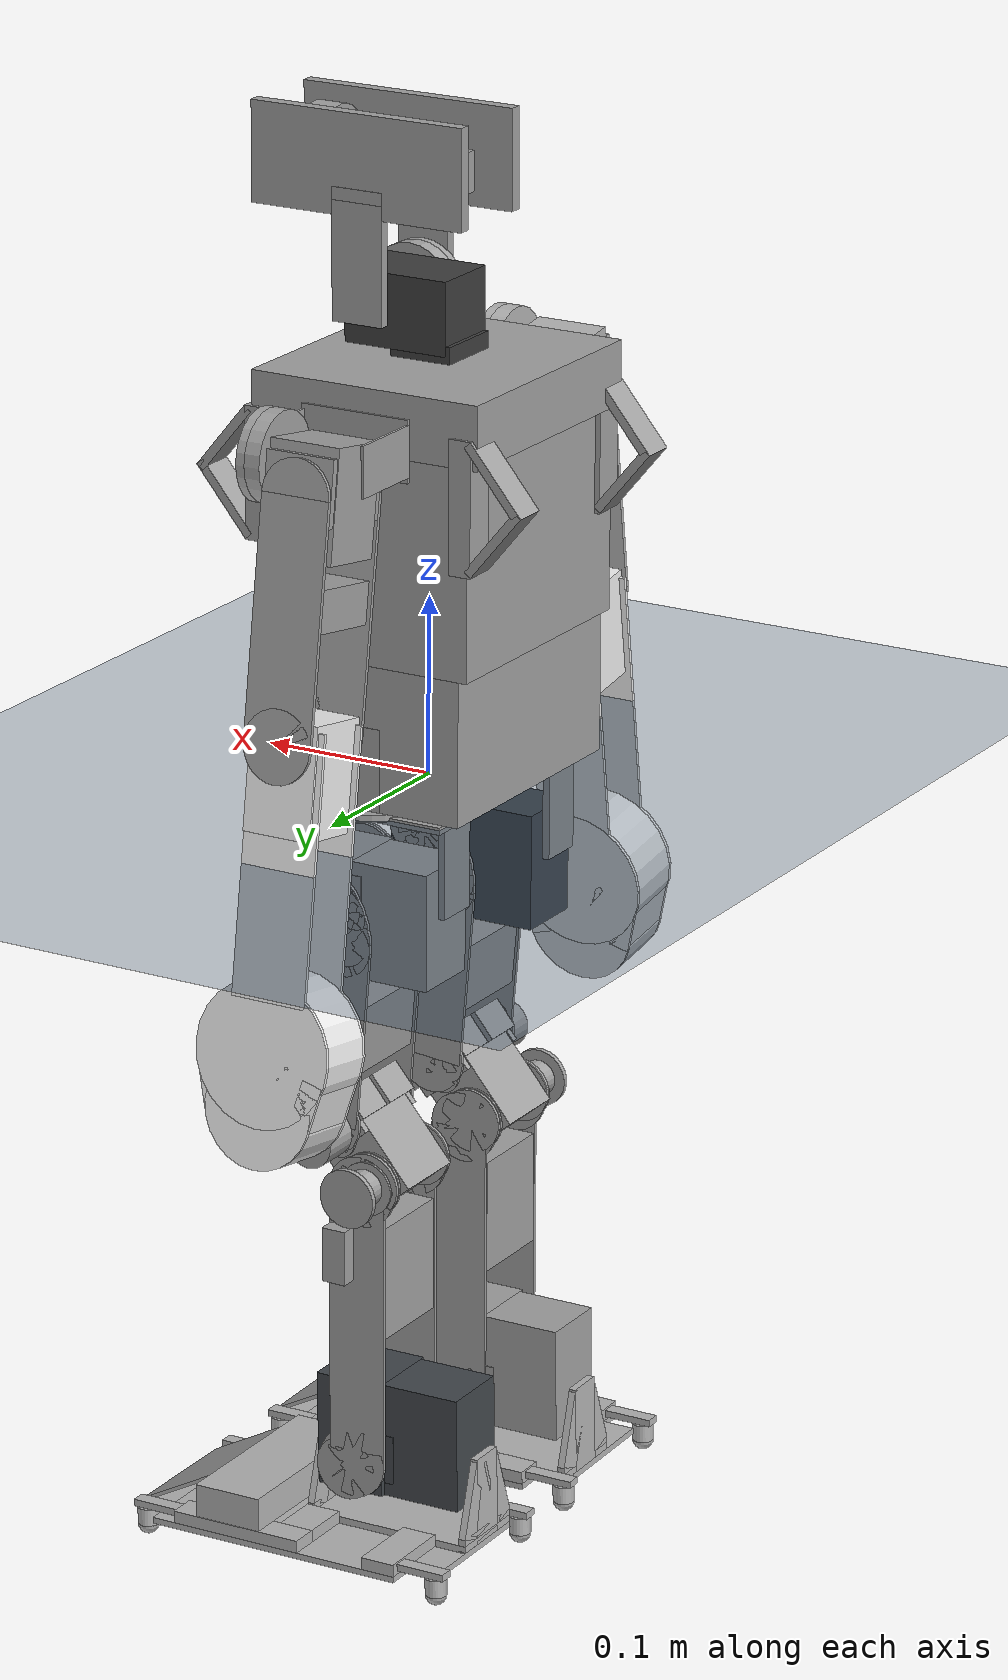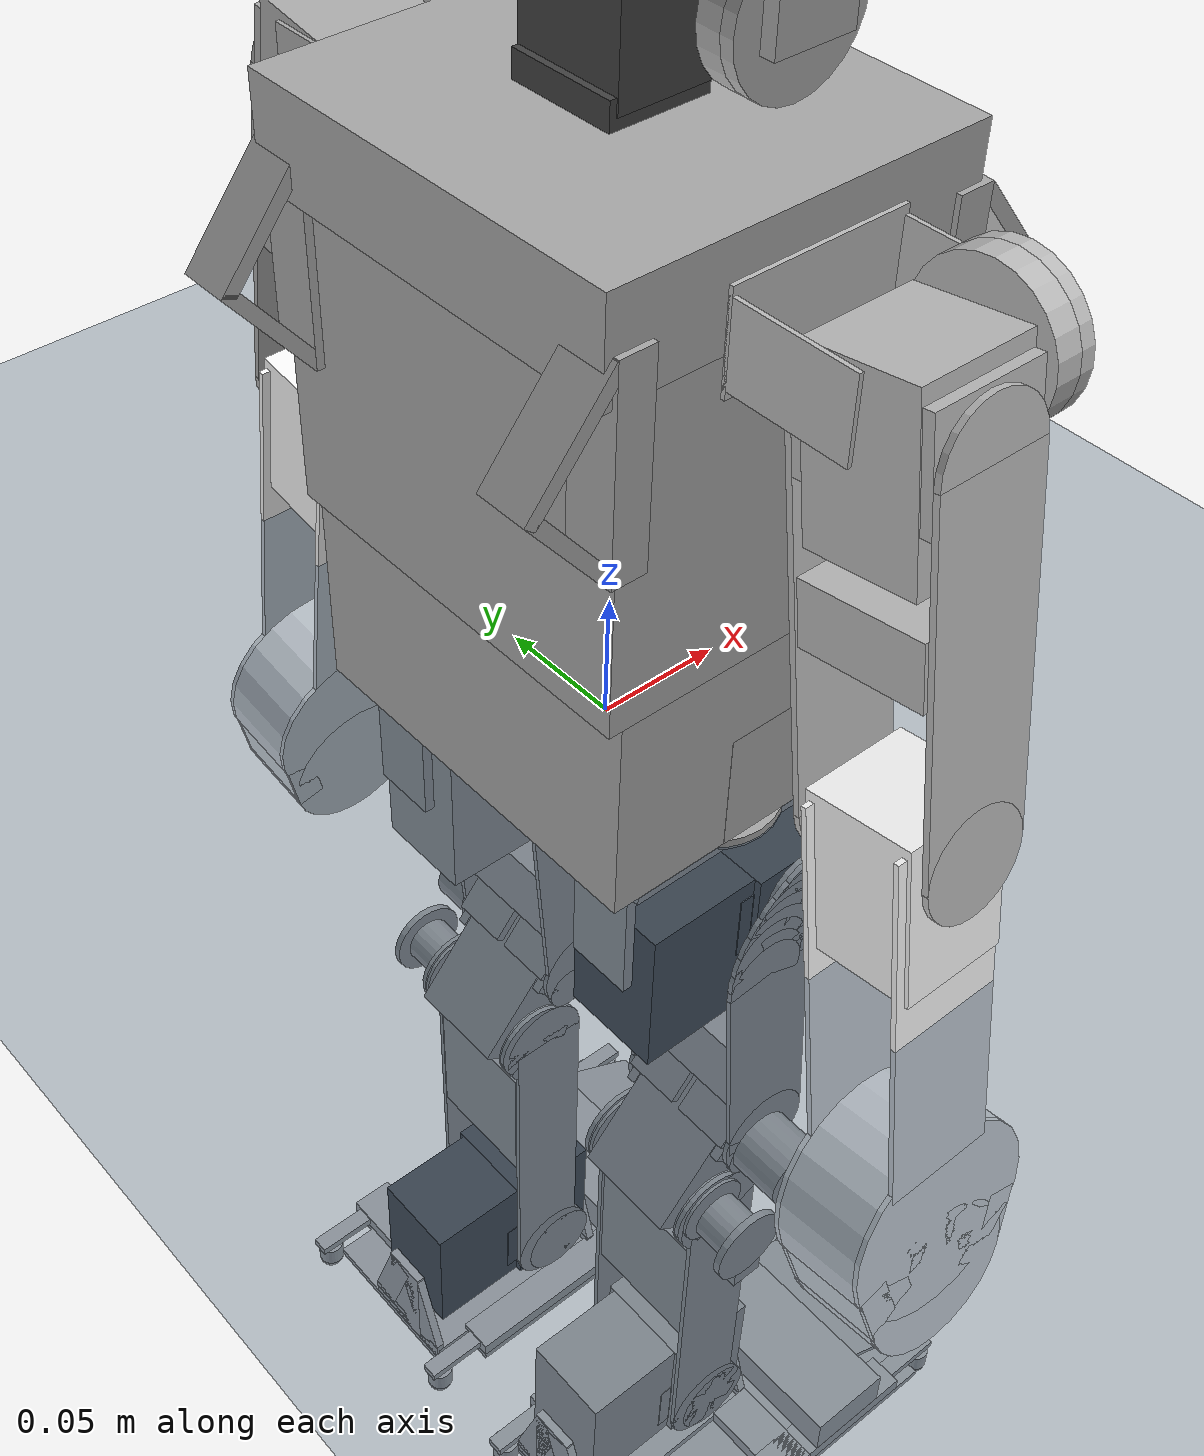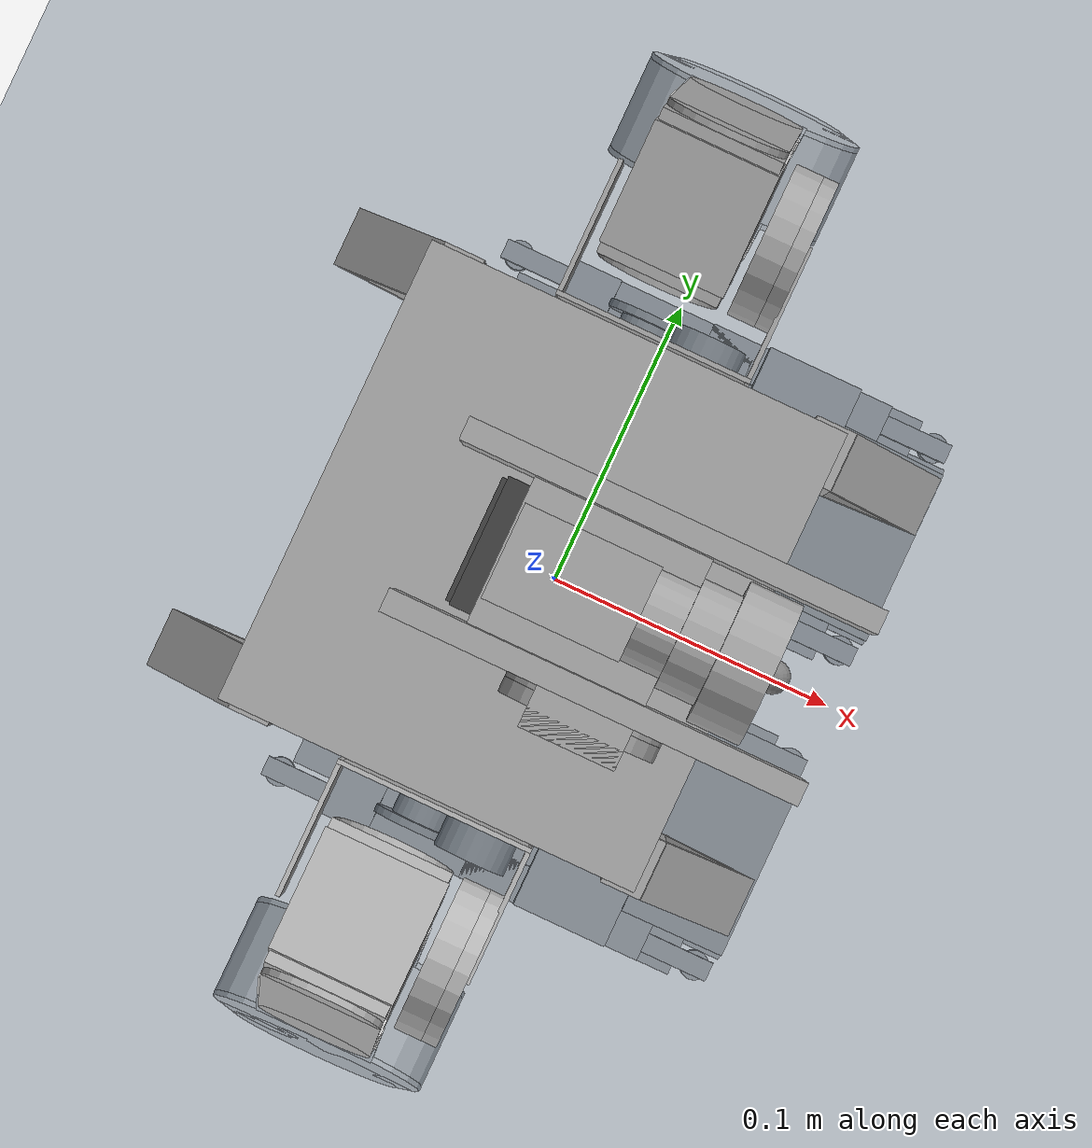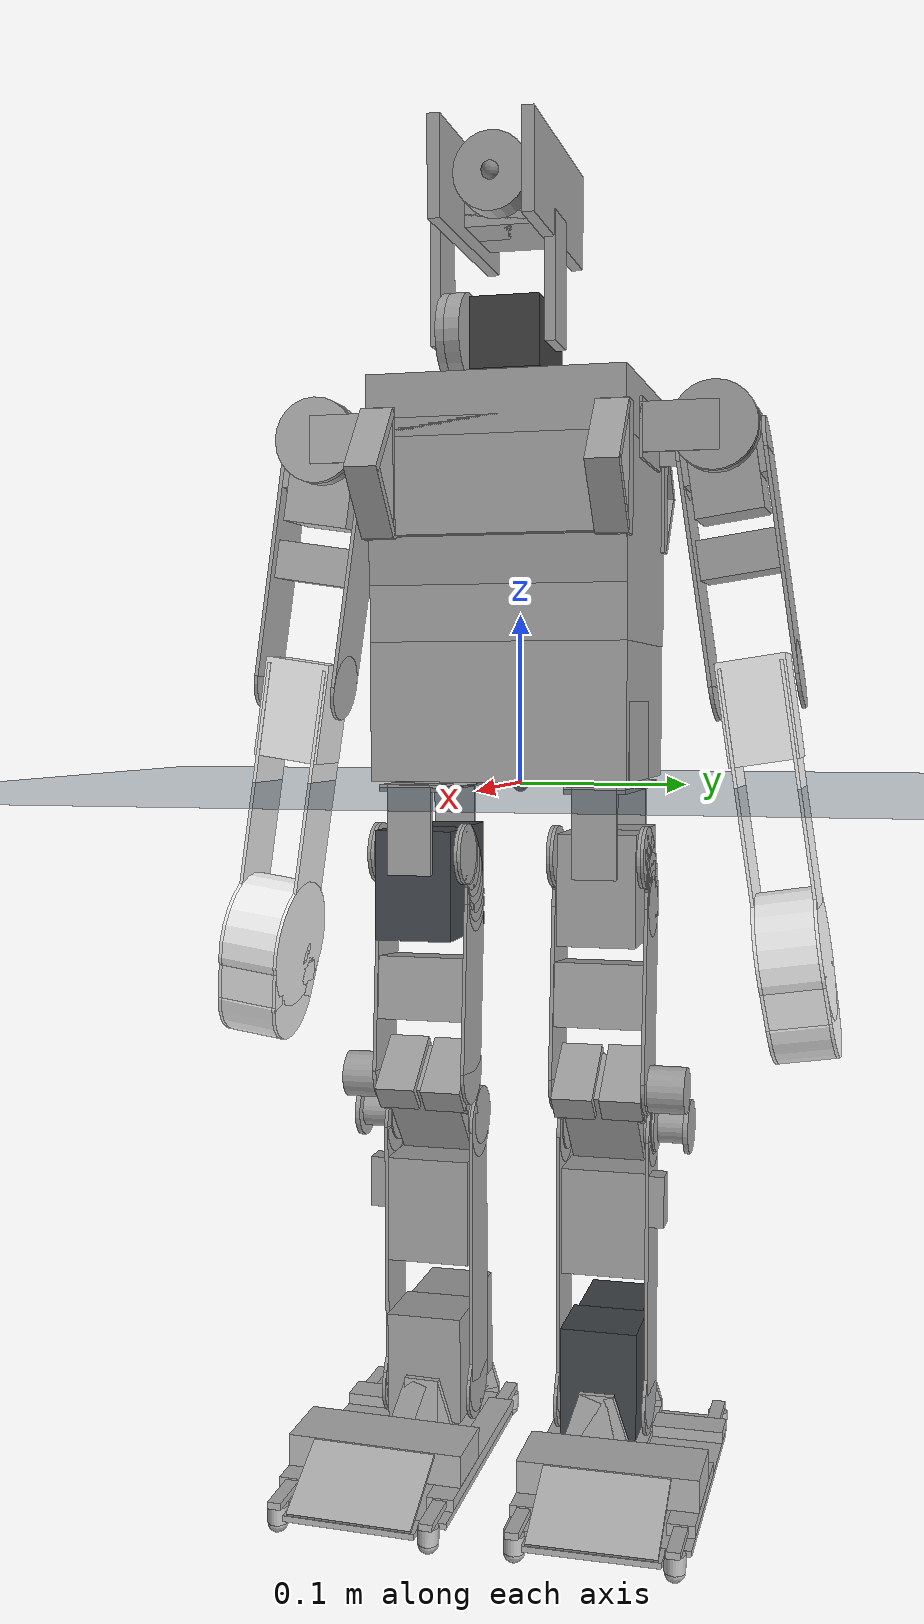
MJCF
<mujoco model="wolfgang">
	<include file="wolfgang.xml" />
    <size memory="150M"/>

	<visual>
		<headlight diffuse="0.6 0.6 0.6" ambient="0.3 0.3 0.3" specular="0 0 0"/>
		<rgba haze="0.15 0.25 0.35 1"/>
		<global azimuth="160" elevation="-20"/>
	</visual>

	<asset>
		<texture type="skybox" builtin="gradient" rgb1="0.3 0.5 0.7" rgb2="0 0 0" width="512" height="3072"/>
		<texture type="2d" name="groundplane" builtin="checker" mark="edge" rgb1="0.2 0.3 0.4" rgb2="0.1 0.2 0.3"
			markrgb="0.8 0.8 0.8" width="300" height="300"/>
		<material name="groundplane" texture="groundplane" texuniform="true" texrepeat="5 5" reflectance="0.2"/>
	</asset>

	<worldbody>
		<light pos="0 0 3.5" dir="0 0 -1" directional="true"/>
		<geom name="floor" size="0 0 0.05" pos="0 0 0" type="plane" material="groundplane"/>

	</worldbody>
</mujoco>

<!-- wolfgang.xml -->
<mujoco model="wolfgang">
  <compiler angle="radian"/>
  <default>
        <default class="mx106">
            <position kp="21" forcerange="-8 8" />
            <joint damping="1.7" armature="0.025" frictionloss="0.10" />
        </default>
        <default class="mx64">
            <position kp="12.5" forcerange="-5 5" />
            <joint damping="0.66" armature="0.012" frictionloss="0.09" />
        </default>
		<default class="xm430">
            <position kp="21.1" ctrlrange="-3.141592 3.141592" forcerange="-5 5"/>
            <joint damping="1.084" armature="0.045" frictionloss="0.03"/>
        </default>

    <default class="mx64-14">
            <position kp="12.5" forcerange="-7.3 7.3" />
            <joint damping="0.65" armature="0.012" frictionloss="0.09" />
        </default>

    <default class="mx106-14">
            <position kp="21" forcerange="-10 10" />
            <joint damping="1.7" armature="0.025" frictionloss="0.10" />
        </default>
    <default class="xh540">
            <position kp="21" forcerange="-11.7 11.7" />
            <joint damping="1.7" armature="0.025" frictionloss="0.10" />
        </default>
    </default>
	<option noslip_iterations="1"></option>

  <worldbody>
    <body name="torso_2023" >
      <freejoint name="root" />
      <site name="torso"  pos=" 0 0 0.15"/>
      <site name="trunk" />
        <inertial pos="-0.00564376 -0.0026297 0.109553" quat="0.997756 0.00472747 0.0649963 -0.0153334" mass="2.0839" diaginertia="0.0185762 0.0158759 0.00761796"/>
        <geom size="0.0201 0.0205 0.03055" pos="0.01605 0.053 0.2035" quat="9.38184e-07 -0.707105 9.38187e-07 0.707108" type="box" rgba="0.647059 0.647059 0.647059 1"/>
        <geom size="0.0201 0.0205 0.03055" pos="0.01605 -0.053 0.2035" quat="0.707105 0 -0.707108 0" type="box" rgba="0.647059 0.647059 0.647059 1"/>
        <geom size="0.0095 0.0365 0.0065" pos="-0.0635 0.0675 0.177415" quat="0.499998 -0.5 -0.500002 0.5" type="box" rgba="0.647059 0.647059 0.647059 1"/>
        <geom size="0.0095 0.0234397 0.0025" pos="-0.0831853 0.0675 0.193936" quat="0.30209 0.639328 0.63933 0.302091" type="box" rgba="0.647059 0.647059 0.647059 1"/>
        <geom size="0.0095 0.0234397 0.0025" pos="-0.0831853 0.0675 0.160894" quat="0.30209 -0.639328 -0.63933 0.302091" type="box" rgba="0.647059 0.647059 0.647059 1"/>
        <geom size="0.07 0.02 0.022" pos="-0.0375 -0.0035 0.0295" quat="0.707105 0 0 -0.707108" type="box" rgba="0.647059 0.647059 0.647059 1"/>
        <geom size="0.0201 0.023 0.03255" pos="0.01805 -0.055 0.026" quat="0.499998 0.5 -0.500002 -0.5" type="box" rgba="0.647059 0.647059 0.647059 1"/>
        <geom size="0.0095 0.0365 0.0065" pos="0.0595 0.0675 0.177415" quat="0.499998 -0.5 0.500002 -0.5" type="box" rgba="0.647059 0.647059 0.647059 1"/>
        <geom size="0.0095 0.0234397 0.0025" pos="0.0791853 0.0675 0.193936" quat="0.30209 0.639328 -0.63933 -0.302091" type="box" rgba="0.647059 0.647059 0.647059 1"/>
        <geom size="0.0095 0.0234397 0.0025" pos="0.0791853 0.0675 0.160894" quat="0.30209 -0.639328 0.63933 -0.302091" type="box" rgba="0.647059 0.647059 0.647059 1"/>
        <geom size="0.0201 0.023 0.03255" pos="0.01805 0.055 0.026" quat="0.499998 0.5 -0.500002 -0.5" type="box" rgba="0.647059 0.647059 0.647059 1"/>
        <geom size="0.06 0.075 0.04" pos="-0.002 0 0.043" type="box" rgba="0.647059 0.647059 0.647059 1"/>
        <geom size="0.0201 0.0205 0.03055" pos="0.00805 0 0.211" quat="0.499998 -0.5 -0.500002 0.5" type="box" rgba="0.647059 0.647059 0.647059 1"/>
        <geom size="0.0095 0.0365 0.0065" pos="-0.0635 -0.0675 0.177415" quat="0.499998 -0.5 -0.500002 0.5" type="box" rgba="0.647059 0.647059 0.647059 1"/>
        <geom size="0.0095 0.0234397 0.0025" pos="-0.0831853 -0.0675 0.193936" quat="0.30209 0.639328 0.63933 0.302091" type="box" rgba="0.647059 0.647059 0.647059 1"/>
        <geom size="0.0095 0.0234397 0.0025" pos="-0.0831853 -0.0675 0.160894" quat="0.30209 -0.639328 -0.63933 0.302091" type="box" rgba="0.647059 0.647059 0.647059 1"/>
        <geom size="0.0095 0.0365 0.0065" pos="0.0595 -0.0675 0.177415" quat="0.499998 -0.5 0.500002 -0.5" type="box" rgba="0.647059 0.647059 0.647059 1"/>
        <geom size="0.0095 0.0234397 0.0025" pos="0.0791853 -0.0675 0.193936" quat="0.30209 0.639328 -0.63933 -0.302091" type="box" rgba="0.647059 0.647059 0.647059 1"/>
        <geom size="0.0095 0.0234397 0.0025" pos="0.0791853 -0.0675 0.160894" quat="0.30209 -0.639328 0.63933 -0.302091" type="box" rgba="0.647059 0.647059 0.647059 1"/>
        <geom size="0.075 0.0625 0.0575" pos="-0.0045 0 0.1405" quat="0.707105 0 0 0.707108" type="box" rgba="0.647059 0.647059 0.647059 1"/>
        <geom size="0.075 0.005 0.0273829" pos="0.053 0 0.115383" quat="0.706352 0.0326317 0.0326318 0.706355" type="box" rgba="0.647059 0.647059 0.647059 1"/>
        <geom size="0.075 0.005 0.0327252" pos="0.058 0 0.175725" quat="0.707105 0 0 0.707108" type="box" rgba="0.647059 0.647059 0.647059 1"/>
        <geom size="0.075 0.068 0.0175" pos="-0.005 0 0.2155" quat="0.707105 0 0 0.707108" type="box" rgba="0.647059 0.647059 0.647059 1"/>
        <body name="imu_frame_uncalibrated" pos="-0.0369749 -0.0474614 0.224" quat="1 0 0 0">
          <inertial pos="0 0 0" mass="1e-09" diaginertia="0 0 0"/>
        </body>
        <body name="r_shoulder" pos="-0.0015 -0.0765 0.2035" quat="1.32679e-06 0 0 -1">
          <inertial pos="-0.0135397 0.0284022 -1.54699e-06" quat="0.180501 0.68368 -0.180422 0.683703" mass="0.041445" diaginertia="3.49573e-05 3.19948e-05 1.42174e-05"/>
          <joint class="mx64-14" name="right_shoulder_pitch" pos="0 0 0" axis="0 -1 0"  />
          <geom size="0.025 0.0025" pos="-0.02845 0.042 0" quat="0.499998 -0.5 -0.500002 0.5" type="cylinder" rgba="0.717647 0.717647 0.717647 1"/>
          <geom size="0.025 0.0045" pos="-0.02145 0.042 0" quat="0.499998 -0.5 -0.500002 0.5" type="cylinder" rgba="0.717647 0.717647 0.717647 1"/>
          <geom size="0.03195 0.00075 0.017" pos="0 0.00075 0" type="box" rgba="0.717647 0.717647 0.717647 1"/>
          <geom size="0.00075 0.0225 0.014" pos="0.0312 0.0225 0" type="box" rgba="0.717647 0.717647 0.717647 1"/>
          <geom size="0.00075 0.0225 0.014" pos="-0.0312 0.0225 0" type="box" rgba="0.717647 0.717647 0.717647 1"/>
          <body name="r_upper_arm" pos="-0.01695 0.042 0" euler="1.5707963 -1.5707963 -0.15">
            <inertial pos="9.77435e-05 -0.0325821 -0.0239229" quat="0.493157 0.506993 -0.500259 0.499495" mass="0.228498" diaginertia="0.000371168 0.000241466 0.00017944"/>
            <joint class="mx64-14" name="right_shoulder_roll" pos="0 0 0" axis="0 0 -1"  />
            <geom size="0.0201 0.0205 0.03055" pos="0 -0.01755 -0.0235" quat="0.707105 -0.707108 0 0" type="box" rgba="0.717647 0.717647 0.717647 1"/>
            <geom size="0.02 0.001125" pos="0.025125 -0.144 -0.0235" quat="0.707105 0 -0.707108 0" type="cylinder" rgba="0.717647 0.717647 0.717647 1"/>
            <geom size="0.02 0.001125" pos="0.025125 -0.014 -0.0235" quat="0.707105 0 -0.707108 0" type="cylinder" rgba="0.717647 0.717647 0.717647 1"/>
            <geom size="0.02 0.001125 0.065" pos="0.025125 -0.079 -0.0235" quat="0.499998 -0.5 -0.5 -0.500002" type="box" rgba="0.717647 0.717647 0.717647 1"/>
            <geom size="0.018 0.02 0.00465" pos="-0.01935 -0.0105 -0.0235" quat="0.499998 -0.5 -0.500002 0.5" type="box" rgba="0.717647 0.717647 0.717647 1"/>
            <geom size="0.02 0.001125" pos="-0.025125 -0.144 -0.0235" quat="0.707105 0 0.707108 0" type="cylinder" rgba="0.717647 0.717647 0.717647 1"/>
            <geom size="0.02 0.001125" pos="-0.025125 -0.014 -0.0235" quat="0.707105 0 0.707108 0" type="cylinder" rgba="0.717647 0.717647 0.717647 1"/>
            <geom size="0.02 0.001125 0.065" pos="-0.025125 -0.079 -0.0235" quat="0.499998 -0.5 0.5 0.500002" type="box" rgba="0.717647 0.717647 0.717647 1"/>
            <geom size="0.018 0.02 0.00465" pos="0.01935 -0.0105 -0.0235" quat="0.499998 0.5 0.500002 0.5" type="box" rgba="0.717647 0.717647 0.717647 1"/>
            <geom size="0.0188 0.0115 0.023" pos="0.001 -0.0715 -0.023699" quat="0.707105 0 -0.707108 0" type="box" rgba="0.717647 0.717647 0.717647 1"/>
            <body name="r_lower_arm" pos="0.024 -0.144 -0.0235" euler="-1.5707923 1.5708003 1.5708003">
              <inertial pos="0.000436307 -0.0605126 -0.0235553" quat="0.500185 0.49962 -0.500396 0.499799" mass="0.207774" diaginertia="0.00110076 0.001088 8.9031e-05"/>
              <joint class="mx64-14" name="right_elbow" pos="0 0 0" axis="0 0 1"  />
              <geom size="0.04 0.001" pos="0 -0.163682 -0.0055" quat="1.32679e-06 0 0 -1" type="cylinder" rgba="0.960784 0.960784 0.960784 1"/>
              <geom size="0.022 0.001 0.0725" pos="0.0015 -0.0631823 -0.0055" quat="9.38184e-07 -9.38187e-07 0.707108 -0.707105" type="box" rgba="0.960784 0.960784 0.960784 1"/>
              <geom size="0.032 0.001" pos="0 -0.193682 -0.0055" quat="1.32679e-06 0 0 -1" type="cylinder" rgba="0.960784 0.960784 0.960784 1"/>
              <geom size="0.006 0.001 0.0145" pos="-0.0282 -0.187682 -0.0055" quat="0.701469 -0.701472 -0.0891014 0.089101" type="box" rgba="0.960784 0.960784 0.960784 1"/>
              <geom size="0.006 0.001 0.0145" pos="0.0282 -0.187682 -0.0055" quat="0.701469 -0.701472 0.0891014 -0.089101" type="box" rgba="0.960784 0.960784 0.960784 1"/>
              <geom size="0.0201 0.0205 0.03055" pos="0 -0.01755 -0.0235" quat="0.707105 -0.707108 0 0" type="box" rgba="0.960784 0.960784 0.960784 1"/>
              <geom size="0.04 0.017" pos="0 -0.163682 -0.0235" quat="1.32679e-06 -1 0 0" type="cylinder" rgba="0.960784 0.960784 0.960784 1"/>
              <geom size="0.032 0.017" pos="0 -0.193682 -0.0235" quat="1.32679e-06 -1 0 0" type="cylinder" rgba="0.960784 0.960784 0.960784 1"/>
              <geom size="0.006 0.017 0.0145" pos="0.0282 -0.187682 -0.0235" quat="0.0891027 0.089103 0.701472 0.701469" type="box" rgba="0.960784 0.960784 0.960784 1"/>
              <geom size="0.006 0.017 0.0145" pos="-0.0282 -0.187682 -0.0235" quat="0.0891027 0.089103 -0.701472 -0.701469" type="box" rgba="0.960784 0.960784 0.960784 1"/>
              <geom size="0.04 0.001" pos="0 -0.163682 -0.0415" quat="1.32679e-06 0 0 -1" type="cylinder" rgba="0.960784 0.960784 0.960784 1"/>
              <geom size="0.022 0.001 0.0725" pos="0.0015 -0.0631823 -0.0415" quat="9.38184e-07 -9.38187e-07 0.707108 -0.707105" type="box" rgba="0.960784 0.960784 0.960784 1"/>
              <geom size="0.032 0.001" pos="0 -0.193682 -0.0415" quat="1.32679e-06 0 0 -1" type="cylinder" rgba="0.960784 0.960784 0.960784 1"/>
              <geom size="0.006 0.001 0.0145" pos="-0.0282 -0.187682 -0.0415" quat="0.701469 -0.701472 -0.0891014 0.089101" type="box" rgba="0.960784 0.960784 0.960784 1"/>
              <geom size="0.006 0.001 0.0145" pos="0.0282 -0.187682 -0.0415" quat="0.701469 -0.701472 0.0891014 -0.089101" type="box" rgba="0.960784 0.960784 0.960784 1"/>
              <body name="r_wrist" pos="0 -0.226182 -0.0235" quat="0.499998 0.5 -0.500002 -0.5">
                <inertial pos="0 0 0" mass="1e-09" diaginertia="0 0 0"/>
              </body>
            </body>
          </body>
        </body>
        <body name="l_shoulder" pos="-0.0015 0.0765 0.2035" quat="1.7603e-12 -1.32679e-06 -1 1.32679e-06">
          <inertial pos="-0.0135397 0.0284022 1.54699e-06" quat="0.180422 0.683703 -0.180501 0.68368" mass="0.041445" diaginertia="3.49573e-05 3.19948e-05 1.42174e-05"/>
          <joint class="mx64-14" name="left_shoulder_pitch" pos="0 0 0" axis="0 1 0"  />
          <geom size="0.025 0.0025" pos="-0.02845 0.042 0" quat="0.499998 0.5 -0.500002 -0.5" type="cylinder" rgba="0.647059 0.647059 0.647059 1"/>
          <geom size="0.03195 0.00075 0.017" pos="0 0.00075 0" type="box" rgba="0.647059 0.647059 0.647059 1"/>
          <geom size="0.00075 0.0225 0.014" pos="0.0312 0.0225 0" type="box" rgba="0.647059 0.647059 0.647059 1"/>
          <geom size="0.00075 0.0225 0.014" pos="-0.0312 0.0225 0" type="box" rgba="0.647059 0.647059 0.647059 1"/>
          <geom size="0.025 0.0045" pos="-0.02145 0.042 0" quat="0.499998 0.5 -0.500002 -0.5" type="cylinder" rgba="0.647059 0.647059 0.647059 1"/>
          <body name="l_upper_arm" pos="-0.01695 0.042 0" euler="-0.15 -1.5707963 1.5707963">
            <inertial pos="9.77435e-05 -0.0325821 -0.0239229" quat="0.493157 0.506993 -0.500259 0.499495" mass="0.228498" diaginertia="0.000371168 0.000241466 0.00017944"/>
            <joint class="mx64-14" name="left_shoulder_roll" pos="0 0 0" axis="0 0 -1"  />
            <geom size="0.0201 0.0205 0.03055" pos="0 -0.01755 -0.0235" quat="0.707105 -0.707108 0 0" type="box" rgba="0.647059 0.647059 0.647059 1"/>
            <geom size="0.018 0.02 0.00465" pos="-0.01935 -0.0105 -0.0235" quat="0.499998 -0.5 -0.500002 0.5" type="box" rgba="0.647059 0.647059 0.647059 1"/>
            <geom size="0.018 0.02 0.00465" pos="0.01935 -0.0105 -0.0235" quat="0.499998 0.5 0.500002 0.5" type="box" rgba="0.647059 0.647059 0.647059 1"/>
            <geom size="0.0188 0.0115 0.023" pos="0.001 -0.0715 -0.023699" quat="0.707105 0 -0.707108 0" type="box" rgba="0.647059 0.647059 0.647059 1"/>
            <geom size="0.02 0.001125" pos="-0.025125 -0.144 -0.0235" quat="0.707105 0 0.707108 0" type="cylinder" rgba="0.647059 0.647059 0.647059 1"/>
            <geom size="0.02 0.001125" pos="-0.025125 -0.014 -0.0235" quat="0.707105 0 0.707108 0" type="cylinder" rgba="0.647059 0.647059 0.647059 1"/>
            <geom size="0.02 0.001125 0.065" pos="-0.025125 -0.079 -0.0235" quat="0.499998 -0.5 0.5 0.500002" type="box" rgba="0.647059 0.647059 0.647059 1"/>
            <geom size="0.02 0.001125" pos="0.025125 -0.144 -0.0235" quat="0.707105 0 -0.707108 0" type="cylinder" rgba="0.647059 0.647059 0.647059 1"/>
            <geom size="0.02 0.001125" pos="0.025125 -0.014 -0.0235" quat="0.707105 0 -0.707108 0" type="cylinder" rgba="0.647059 0.647059 0.647059 1"/>
            <geom size="0.02 0.001125 0.065" pos="0.025125 -0.079 -0.0235" quat="0.499998 -0.5 -0.5 -0.500002" type="box" rgba="0.647059 0.647059 0.647059 1"/>
            <body name="l_lower_arm" pos="-0.024 -0.144 -0.0235" euler="1.5707923 -1.5708003 1.5708003">
              <inertial pos="-0.000436306 -0.0605126 -0.0235553" quat="0.502963 0.497233 -0.502767 0.497003" mass="0.207774" diaginertia="0.00110076 0.00108813 8.89004e-05"/>
              <joint class="mx64-14" name="left_elbow" pos="0 0 0" axis="0 0 -1" />
              <geom size="0.0201 0.0205 0.03055" pos="0 -0.01755 -0.0235" quat="0.707105 -0.707108 0 0" type="box" rgba="0.960784 0.960784 0.960784 1"/>
              <geom size="0.04 0.001" pos="0 -0.163682 -0.0415" quat="1.32679e-06 -1 0 0" type="cylinder" rgba="0.960784 0.960784 0.960784 1"/>
              <geom size="0.022 0.001 0.0725" pos="-0.0015 -0.0631823 -0.0415" quat="0.707105 0.707108 0 0" type="box" rgba="0.960784 0.960784 0.960784 1"/>
              <geom size="0.032 0.001" pos="0 -0.193682 -0.0415" quat="1.32679e-06 -1 0 0" type="cylinder" rgba="0.960784 0.960784 0.960784 1"/>
              <geom size="0.006 0.001 0.0145" pos="0.0282 -0.187682 -0.0415" quat="0.0891027 0.089103 0.701472 0.701469" type="box" rgba="0.960784 0.960784 0.960784 1"/>
              <geom size="0.006 0.001 0.0145" pos="-0.0282 -0.187682 -0.0415" quat="0.0891027 0.089103 -0.701472 -0.701469" type="box" rgba="0.960784 0.960784 0.960784 1"/>
              <geom size="0.04 0.017" pos="0 -0.163682 -0.0235" quat="1.32679e-06 0 0 -1" type="cylinder" rgba="0.960784 0.960784 0.960784 1"/>
              <geom size="0.032 0.017" pos="0 -0.193682 -0.0235" quat="1.32679e-06 0 0 -1" type="cylinder" rgba="0.960784 0.960784 0.960784 1"/>
              <geom size="0.006 0.017 0.0145" pos="-0.0282 -0.187682 -0.0235" quat="0.701469 -0.701472 -0.0891014 0.089101" type="box" rgba="0.960784 0.960784 0.960784 1"/>
              <geom size="0.006 0.017 0.0145" pos="0.0282 -0.187682 -0.0235" quat="0.701469 -0.701472 0.0891014 -0.089101" type="box" rgba="0.960784 0.960784 0.960784 1"/>
              <geom size="0.04 0.001" pos="0 -0.163682 -0.0055" quat="1.32679e-06 -1 0 0" type="cylinder" rgba="0.960784 0.960784 0.960784 1"/>
              <geom size="0.022 0.001 0.0725" pos="-0.0015 -0.0631823 -0.0055" quat="0.707105 0.707108 0 0" type="box" rgba="0.960784 0.960784 0.960784 1"/>
              <geom size="0.032 0.001" pos="0 -0.193682 -0.0055" quat="1.32679e-06 -1 0 0" type="cylinder" rgba="0.960784 0.960784 0.960784 1"/>
              <geom size="0.006 0.001 0.0145" pos="0.0282 -0.187682 -0.0055" quat="0.0891027 0.089103 0.701472 0.701469" type="box" rgba="0.960784 0.960784 0.960784 1"/>
              <geom size="0.006 0.001 0.0145" pos="-0.0282 -0.187682 -0.0055" quat="0.0891027 0.089103 -0.701472 -0.701469" type="box" rgba="0.960784 0.960784 0.960784 1"/>
              <body name="l_wrist" pos="0 -0.225182 -0.0235" quat="0.499998 -0.5 0.500002 -0.5">
                <inertial pos="0 0 0" mass="1e-09" diaginertia="0 0 0"/>
              </body>
            </body>
          </body>
        </body>
        <body name="r_hip_1" pos="0 -0.055 0" quat="0.707105 -0.707108 0 0">
          <inertial pos="1.20984e-11 0.010315 -1.06799e-07" quat="-6.86297e-06 0.707107 -6.86297e-06 0.707107" mass="0.0689735" diaginertia="0.000110523 0.00010714 2.18955e-05"/>
          <joint class="mx106-14" name="right_hip_yaw" pos="0 0 0" axis="0 1 0" range="-1.5708 1.5708" />
          <geom size="0.018 0.05 0.002" pos="0 0.0014 0" quat="0.499998 -0.5 0.5 0.500002" type="box" rgba="0.647059 0.647059 0.647059 1"/>
          <geom size="0.0130115 0.002 0.0265" pos="-0.048 0.0259 0" quat="0.499998 -0.5 0.5 0.500002" type="box" rgba="0.647059 0.647059 0.647059 1"/>
          <geom size="0.0130115 0.002 0.0265" pos="0.048 0.0259 0" quat="0.499998 -0.5 0.5 0.500002" type="box" rgba="0.647059 0.647059 0.647059 1"/>
          <geom size="0.025 0.002" pos="0 -0.0006 0.002" quat="0.499998 -0.5 0.5 0.500002" type="cylinder" rgba="0.647059 0.647059 0.647059 1"/>
          <body name="r_hip_2" pos="-0.046 0.0414 0" quat="9.38184e-07 -0.707105 9.38187e-07 0.707108">
            <inertial pos="1.38724e-05 -0.0155281 -0.0486407" quat="0.99678 0.0129755 -0.00329376 0.0790604" mass="0.319807" diaginertia="0.000268643 0.000268139 0.000121226"/>
            <joint class="mx106-14" name="right_hip_roll" pos="0 0 0" axis="0 0 -1" range="-1.9 1.6" />
            <geom size="0.0201 0.023 0.03255" pos="0 -0.01805 -0.026" quat="0.707105 -0.707108 0 0" type="box" rgba="0.262745 0.282353 0.301961 1"/>
            <geom size="0.014 0.003 0.00285" pos="-0.0175 -0.007 -0.04585" quat="9.38184e-07 -0.707105 -0.707108 9.38187e-07" type="box" rgba="0.262745 0.282353 0.301961 1"/>
            <geom size="0.014 0.00175 0.00295" pos="-0.01875 -0.007 -0.05165" quat="9.38184e-07 -0.707105 -0.707108 9.38187e-07" type="box" rgba="0.262745 0.282353 0.301961 1"/>
            <geom size="0.014 0.003 0.00285" pos="0.0175 -0.007 -0.04585" quat="9.38184e-07 -0.707105 0.707108 -9.38187e-07" type="box" rgba="0.262745 0.282353 0.301961 1"/>
            <geom size="0.014 0.00175 0.00295" pos="0.01875 -0.007 -0.05165" quat="9.38184e-07 -0.707105 0.707108 -9.38187e-07" type="box" rgba="0.262745 0.282353 0.301961 1"/>
            <geom size="0.0201 0.023 0.03255" pos="0 -0.01805 -0.0691" quat="0.499998 -0.5 -0.5 -0.500002" type="box" rgba="0.262745 0.282353 0.301961 1"/>
            <body name="r_upper_leg" pos="-0.0265 0 -0.0691" euler="-1.745 0 1.57">
              <inertial pos="0.00493985 -0.0283223 -0.133144" quat="0.995752 -0.00919328 -0.0209573 0.0891915" mass="0.242311" diaginertia="0.000503914 0.000457532 0.000112612"/>
              <joint class="mx106-14" name="right_hip_pitch" pos="0 0 0" axis="0 1 0" range="-2.77 0.79" />
              <geom size="0.021 0.0089913 0.01225" pos="0.0157399 -0.04075 -0.134486" quat="0.183014 0.183012 -0.683014 0.683011" type="box" rgba="0.647059 0.647059 0.647059 1"/>
              <geom size="0.017 0.0124063 0.002" pos="0.0140324 -0.051 -0.137444" quat="0.183014 0.183012 -0.683014 0.683011" type="box" rgba="0.647059 0.647059 0.647059 1"/>
              <geom size="0.018 0.001" pos="0 0.001 0" quat="0.707105 0.707108 0 0" type="cylinder" rgba="0.647059 0.647059 0.647059 1"/>
              <geom size="0.01 0.001" pos="0.009329 0.001 -0.143" quat="0.707105 0.707108 0 0" type="cylinder" rgba="0.647059 0.647059 0.647059 1"/>
              <geom size="0.02 0.001" pos="0.0148403 0.001 -0.132659" quat="0.707105 0.707108 0 0" type="cylinder" rgba="0.647059 0.647059 0.647059 1"/>
              <geom size="0.019 0.001 0.0510495" pos="0.00259365 0.001 -0.0830903" quat="0.991445 0 -0.130526 0" type="box" rgba="0.647059 0.647059 0.647059 1"/>
              <geom size="0.005 0.001 0.005" pos="0.00161489 0.001 -0.0253454" quat="0.130526 1.14226e-06 0.991445 1.14226e-06" type="box" rgba="0.647059 0.647059 0.647059 1"/>
              <geom size="0.01 0.001" pos="0.009329 0.001 -0.143" quat="0.707105 0.707108 0 0" type="cylinder" rgba="0.647059 0.647059 0.647059 1"/>
              <geom size="0.017 0.001" pos="-0.00400978 0.001 -0.00242195" quat="0.707105 0.707108 0 0" type="cylinder" rgba="0.647059 0.647059 0.647059 1"/>
              <geom size="0.017 0.001" pos="-0.00770728 0.001 -0.00682845" quat="0.707105 0.707108 0 0" type="cylinder" rgba="0.647059 0.647059 0.647059 1"/>
              <geom size="0.017 0.001" pos="-0.0105834 0.001 -0.0118101" quat="0.707105 0.707108 0 0" type="cylinder" rgba="0.647059 0.647059 0.647059 1"/>
              <geom size="0.017 0.001" pos="-0.0125508 0.001 -0.0172154" quat="0.707105 0.707108 0 0" type="cylinder" rgba="0.647059 0.647059 0.647059 1"/>
              <geom size="0.017 0.001" pos="-0.0135497 0.001 -0.0228803" quat="0.707105 0.707108 0 0" type="cylinder" rgba="0.647059 0.647059 0.647059 1"/>
              <geom size="0.017 0.001" pos="-0.0135497 0.001 -0.0286326" quat="0.707105 0.707108 0 0" type="cylinder" rgba="0.647059 0.647059 0.647059 1"/>
              <geom size="0.017 0.001" pos="-0.0125508 0.001 -0.0342975" quat="0.707105 0.707108 0 0" type="cylinder" rgba="0.647059 0.647059 0.647059 1"/>
              <geom size="0.018 0.001" pos="-2.3657e-07 -0.052 -3.21056e-07" quat="0.183014 0.183012 -0.683014 0.683011" type="cylinder" rgba="0.647059 0.647059 0.647059 1"/>
              <geom size="0.017 0.02925 0.022" pos="0.00382705 -0.0265 -0.15562" quat="0.183014 0.183012 -0.683014 0.683011" type="box" rgba="0.647059 0.647059 0.647059 1"/>
              <geom size="0.014 0.011" pos="0.014 -0.066 -0.138" quat="0.707105 0.707108 0 0" type="cylinder" rgba="0.647059 0.647059 0.647059 1"/>
              <geom size="0.018 0.001" pos="-2.3657e-07 -0.001 -3.21056e-07" quat="0.183014 0.183012 -0.683014 0.683011" type="cylinder" rgba="0.647059 0.647059 0.647059 1"/>
              <geom size="0.018 0.001" pos="0 -0.054 0" quat="0.707105 0.707108 0 0" type="cylinder" rgba="0.647059 0.647059 0.647059 1"/>
              <geom size="0.01 0.001" pos="0.009329 -0.054 -0.143" quat="0.707105 0.707108 0 0" type="cylinder" rgba="0.647059 0.647059 0.647059 1"/>
              <geom size="0.02 0.001" pos="0.0148403 -0.054 -0.132659" quat="0.707105 0.707108 0 0" type="cylinder" rgba="0.647059 0.647059 0.647059 1"/>
              <geom size="0.019 0.001 0.0510495" pos="0.00259365 -0.054 -0.0830903" quat="0.991445 0 -0.130526 0" type="box" rgba="0.647059 0.647059 0.647059 1"/>
              <geom size="0.005 0.001 0.005" pos="0.00161489 -0.054 -0.0253454" quat="0.130526 1.14226e-06 0.991445 1.14226e-06" type="box" rgba="0.647059 0.647059 0.647059 1"/>
              <geom size="0.01 0.001" pos="0.009329 -0.054 -0.143" quat="0.707105 0.707108 0 0" type="cylinder" rgba="0.647059 0.647059 0.647059 1"/>
              <geom size="0.017 0.001" pos="-0.00400978 -0.054 -0.00242195" quat="0.707105 0.707108 0 0" type="cylinder" rgba="0.647059 0.647059 0.647059 1"/>
              <geom size="0.017 0.001" pos="-0.00770728 -0.054 -0.00682845" quat="0.707105 0.707108 0 0" type="cylinder" rgba="0.647059 0.647059 0.647059 1"/>
              <geom size="0.017 0.001" pos="-0.0105834 -0.054 -0.0118101" quat="0.707105 0.707108 0 0" type="cylinder" rgba="0.647059 0.647059 0.647059 1"/>
              <geom size="0.017 0.001" pos="-0.0125508 -0.054 -0.0172154" quat="0.707105 0.707108 0 0" type="cylinder" rgba="0.647059 0.647059 0.647059 1"/>
              <geom size="0.017 0.001" pos="-0.0135497 -0.054 -0.0228803" quat="0.707105 0.707108 0 0" type="cylinder" rgba="0.647059 0.647059 0.647059 1"/>
              <geom size="0.017 0.001" pos="-0.0135497 -0.054 -0.0286326" quat="0.707105 0.707108 0 0" type="cylinder" rgba="0.647059 0.647059 0.647059 1"/>
              <geom size="0.017 0.001" pos="-0.0125508 -0.054 -0.0342975" quat="0.707105 0.707108 0 0" type="cylinder" rgba="0.647059 0.647059 0.647059 1"/>
              <geom size="0.021 0.0089913 0.01225" pos="0.0161729 -0.01225 -0.134736" quat="0.683011 -0.683014 0.183012 0.183013" type="box" rgba="0.647059 0.647059 0.647059 1"/>
              <geom size="0.017 0.0124063 0.002" pos="0.0144654 -0.00200004 -0.137694" quat="0.683011 -0.683014 0.183012 0.183013" type="box" rgba="0.647059 0.647059 0.647059 1"/>
              <geom size="0.017575 0.019 0.0265" pos="0.00281079 -0.0265 -0.0836106" quat="0.0922969 -0.0922947 0.701059 0.701056" type="box" rgba="0.647059 0.647059 0.647059 1"/>
              <body name="r_lower_leg" pos="-0.00392295 -0.051 -0.169043" quat="0.991445 0 -0.130526 0">
                <inertial pos="0.00142428 0.0183569 -0.0617082" quat="0.996507 0.0805308 0.0213013 -0.00583843" mass="0.0880635" diaginertia="0.000284834 0.000243363 7.08604e-05"/>
                <joint class="xh540" name="right_knee" pos="0 0 0" axis="0 1 0"  />
                <geom size="0.018 0.00075" pos="4.35337e-09 0.049 -2.49321e-07" quat="0.707105 0.707108 0 0" type="cylinder" rgba="0.647059 0.647059 0.647059 1"/>
                <geom size="0.018 0.001" pos="0 0.0515 -0.17" quat="0.707105 0.707108 0 0" type="cylinder" rgba="0.647059 0.647059 0.647059 1"/>
                <geom size="0.018 0.001" pos="0 0.0515 0" quat="0.707105 0.707108 0 0" type="cylinder" rgba="0.647059 0.647059 0.647059 1"/>
                <geom size="0.02 0.001" pos="-0.004 0.0515 -0.165" quat="0.707105 0.707108 0 0" type="cylinder" rgba="0.647059 0.647059 0.647059 1"/>
                <geom size="0.02 0.001" pos="0.004 0.0515 -0.005" quat="0.707105 0.707108 0 0" type="cylinder" rgba="0.647059 0.647059 0.647059 1"/>
                <geom size="0.017 0.001 0.08" pos="-9.2229e-05 0.0515 -0.085786" quat="0.999048 0 0.0436194 0" type="box" rgba="0.647059 0.647059 0.647059 1"/>
                <geom size="0.018 0.001" pos="0 -0.0025 -0.17" quat="0.707105 0.707108 0 0" type="cylinder" rgba="0.647059 0.647059 0.647059 1"/>
                <geom size="0.018 0.001" pos="0 -0.0025 0" quat="0.707105 0.707108 0 0" type="cylinder" rgba="0.647059 0.647059 0.647059 1"/>
                <geom size="0.02 0.001" pos="-0.004 -0.0025 -0.165" quat="0.707105 0.707108 0 0" type="cylinder" rgba="0.647059 0.647059 0.647059 1"/>
                <geom size="0.02 0.001" pos="0.004 -0.0025 -0.005" quat="0.707105 0.707108 0 0" type="cylinder" rgba="0.647059 0.647059 0.647059 1"/>
                <geom size="0.017 0.001 0.08" pos="-9.2229e-05 -0.0025 -0.085786" quat="0.999048 0 0.0436194 0" type="box" rgba="0.647059 0.647059 0.647059 1"/>
                <geom size="0.0322425 0.01675 0.0255" pos="0.00253479 0.024 -0.0569148" quat="0.477716 -0.477713 0.521335 0.521332" type="box" rgba="0.647059 0.647059 0.647059 1"/>
                <geom size="0.0165 0.0015" pos="0 -0.024 0" quat="0.707105 0.707108 0 0" type="cylinder" rgba="0.647059 0.647059 0.647059 1"/>
                <geom size="0.0105 0.00815" pos="0 -0.01435 0" quat="0.707105 0.707108 0 0" type="cylinder" rgba="0.647059 0.647059 0.647059 1"/>
                <geom size="0.007 0.00455 0.0155" pos="0.0125977 -0.00805 -0.0413085" quat="-0.0436194 1.38341e-06 0.999048 1.38341e-06" type="box" rgba="0.647059 0.647059 0.647059 1"/>
                <geom size="0.018 0.00075" pos="4.35337e-09 -0.00150002 -2.49321e-07" quat="0.707105 0.707108 0 0" type="cylinder" rgba="0.647059 0.647059 0.647059 1"/>
                <geom size="0.015 0.00135" pos="0 -0.0035 0.00135" quat="0.707105 0.707108 0 0" type="cylinder" rgba="0.647059 0.647059 0.647059 1"/>
                <body name="r_ankle" pos="0 0.0505 -0.17" euler="-1.57 0 0.1">
                  <inertial pos="-0.0204557 -0.0155281 -0.0260036" quat="-0.0712448 0.706639 -0.050439 0.702169" mass="0.319807" diaginertia="0.000272991 0.000268476 0.000116637"/>
                  <joint class="mx106-14" name="right_ankle_pitch" pos="0 0 0" axis="0 0 1"  />
                  <geom size="0.014 0.003 0.00285" pos="-0.02325 -0.007 -0.0435" quat="0.499998 0.5 0.500002 0.5" type="box" rgba="0.647059 0.647059 0.647059 1"/>
                  <geom size="0.014 0.00175 0.00295" pos="-0.01745 -0.007 -0.04475" quat="0.499998 0.5 0.500002 0.5" type="box" rgba="0.647059 0.647059 0.647059 1"/>
                  <geom size="0.0201 0.023 0.03255" pos="-0.0431 -0.01805 -0.026" quat="0.499998 -0.5 -0.5 -0.500002" type="box" rgba="0.647059 0.647059 0.647059 1"/>
                  <geom size="0.014 0.003 0.00285" pos="-0.02325 -0.007 -0.0085" quat="0.499998 -0.5 0.500002 -0.5" type="box" rgba="0.647059 0.647059 0.647059 1"/>
                  <geom size="0.014 0.00175 0.00295" pos="-0.01745 -0.007 -0.00725" quat="0.499998 -0.5 0.500002 -0.5" type="box" rgba="0.647059 0.647059 0.647059 1"/>
                  <geom size="0.0201 0.023 0.03255" pos="0 -0.01805 -0.026" quat="0.707105 -0.707108 0 0" type="box" rgba="0.647059 0.647059 0.647059 1"/>
                  <body name="r_foot" pos="-0.0691 0 -0.026" quat="0.505584 0.494353 0.494351 -0.505586">
                   <site name="right_foot"  pos="-0.02 0.08 -0.0495"/>
                    <inertial pos="0.0119697 0.0911089 -0.0298585" quat="0.514199 0.496212 -0.513987 0.474543" mass="0.26824" diaginertia="0.00115414 0.00088588 0.000315558"/>
                    <joint class="mx106-14" name="right_ankle_roll" pos="0 0 0" axis="0 -1 0" range="-1.4 1.58" />
                    <geom size="0.004 0.02 0.002" pos="-0.03 0.0065 -0.032" quat="1 0 0 0" type="box" rgba="0.717647 0.717647 0.717647 1"/>
                    <geom size="0.024 0.05 0.002" pos="0 0.046 -0.034" type="box" rgba="0.717647 0.717647 0.717647 1"/>
                    <geom size="0.0105 0.002 0.025" pos="0 0.094 -0.011" type="box" rgba="0.717647 0.717647 0.717647 1"/>
                    <geom size="0.0105 0.002 0.025" pos="0 -0.002 -0.011" type="box" rgba="0.717647 0.717647 0.717647 1"/>
                    <geom size="0.024 0.002 0.004" pos="0 -0.002 -0.032" type="box" rgba="0.717647 0.717647 0.717647 1"/>
                    <geom size="0.007 0.002 0.022128" pos="-0.0104 -0.002 -0.0093" quat="0.987173 0 0.159653 0" type="box" rgba="0.717647 0.717647 0.717647 1"/>
                    <geom size="0.007 0.002 0.022128" pos="0.0104 -0.002 -0.0093" quat="0.987173 0 -0.159653 0" type="box" rgba="0.717647 0.717647 0.717647 1"/>
                    <geom size="0.007 0.002 0.022128" pos="-0.0104 0.094 -0.0093" quat="0.987173 0 0.159653 0" type="box" rgba="0.717647 0.717647 0.717647 1"/>
                    <geom size="0.007 0.002 0.022128" pos="0.0104 0.094 -0.0093" quat="0.987173 0 -0.159653 0" type="box" rgba="0.717647 0.717647 0.717647 1"/>
                    <geom size="0.024 0.002 0.004" pos="0 0.094 -0.032" type="box" rgba="0.717647 0.717647 0.717647 1"/>
                    <geom size="0.004 0.02 0.002" pos="0.06 0.1635 -0.032" quat="1 0 0 0" type="box" rgba="0.717647 0.717647 0.717647 1"/>
                    <geom size="0.004 0.02 0.002" pos="-0.03 0.1635 -0.032" quat="1 0 0 0" type="box" rgba="0.717647 0.717647 0.717647 1"/>
                    <geom size="0.077 0.053 0.00175" pos="0.015 0.092 -0.03775" quat="0.707105 0 0 -0.707108" type="box" rgba="0.717647 0.717647 0.717647 1"/>
                    <geom size="0.0095 0.039 0.00175" pos="0.015 0.0055 -0.03775" quat="0.707105 0 0 -0.707108" type="box" rgba="0.717647 0.717647 0.717647 1"/>
                    <geom size="0.008 0.039 0.00175" pos="0.015 0.177 -0.03775" quat="0.707105 0 0 -0.707108" type="box" rgba="0.717647 0.717647 0.717647 1"/>
                    <geom size="0.07 0.008 0.0035" pos="-0.03 0.085 -0.0325" quat="0.707105 0 0 -0.707108" type="box" rgba="0.717647 0.717647 0.717647 1"/>
                    <geom size="0.0395 0.008 0.0035" pos="0.06 0.1155 -0.0325" quat="0.707105 0 0 -0.707108" type="box" rgba="0.717647 0.717647 0.717647 1"/>
                    <geom size="0.01 0.022 0.0035" pos="0.046 0.025 -0.0325" quat="0.707105 0 0 -0.707108" type="box" rgba="0.717647 0.717647 0.717647 1"/>
                    <geom size="0.01 0.022 0.0035" pos="0.046 0.086 -0.0325" quat="0.707105 0 0 -0.707108" type="box" rgba="0.717647 0.717647 0.717647 1"/>
                    <geom size="0.004 0.02 0.002" pos="0.06 0.0065 -0.032" quat="1.32679e-06 0 0 1" type="box" rgba="0.717647 0.717647 0.717647 1"/>
                    <geom size="0.02 0.053 0.0095" pos="0.0149998 0.120225 -0.0192245" quat="0.707105 0 0 -0.707108" type="box" rgba="0.717647 0.717647 0.717647 1"/>
                    <geom size="0.0255 0.037 0.001" pos="0.0149998 0.1625 -0.0232245" quat="0.171497 0.685994 0.685997 -0.171495" type="box" rgba="0.717647 0.717647 0.717647 1"/>
                    <body name="r_sole" pos="0.0152219 0.0907683 -0.0529" quat="0.707105 0 0 0.707108">
                      <inertial pos="0 0 0" mass="1e-09" diaginertia="0 0 0"/>
                    </body>
                    <body name="r_toe" pos="0.015 0.1845 -0.03775" quat="0.707105 0 0 0.707108">
                      <inertial pos="0 0 0" mass="1e-09" diaginertia="0 0 0"/>
                    </body>
                    <body name="rlb" pos="-0.03 -0.007 -0.034" quat="0.707105 0 0 -0.707108">
                      <inertial pos="0 0.000155519 -0.00775879" quat="0.706568 -0.0275971 0.0275971 0.706568" mass="0.00165976" diaginertia="4.44909e-08 4.3352e-08 3.03537e-08"/>
                      <geom size="0.006 0.005" pos="0 0 -0.005" type="cylinder" rgba="0.717647 0.717647 0.717647 1"/>
                      <geom size="0.006" pos="0 0 -0.01" rgba="0.717647 0.717647 0.717647 1"/>
                      <body name="r_cleat_l_back" pos="0 -0.0005 -0.014" quat="1.32679e-06 0 0 -1">
                        <inertial pos="0 0 0" mass="1e-09" diaginertia="0 0 0"/>
                      </body>
                    </body>
                    <body name="rlf" pos="-0.03 0.177 -0.034" quat="0.707105 0 0 -0.707108">
                      <inertial pos="0 0.000155519 -0.00775879" quat="0.706568 -0.0275971 0.0275971 0.706568" mass="0.00165976" diaginertia="4.44909e-08 4.3352e-08 3.03537e-08"/>
                      <geom size="0.006 0.005" pos="0 0 -0.005" type="cylinder" rgba="0.717647 0.717647 0.717647 1"/>
                      <geom size="0.006" pos="0 0 -0.01" rgba="0.717647 0.717647 0.717647 1"/>
                      <body name="r_cleat_l_front" pos="0 -0.0005 -0.014" quat="1.32679e-06 0 0 -1">
                        <inertial pos="0 0 0" mass="1e-09" diaginertia="0 0 0"/>
                      </body>
                    </body>
                    <body name="rrf" pos="0.06 0.177 -0.034" quat="0.707105 0 0 -0.707108">
                      <inertial pos="0 0.000155519 -0.00775879" quat="0.706568 -0.0275971 0.0275971 0.706568" mass="0.00165976" diaginertia="4.44909e-08 4.3352e-08 3.03537e-08"/>
                      <geom size="0.006 0.005" pos="0 0 -0.005" type="cylinder" rgba="0.717647 0.717647 0.717647 1"/>
                      <geom size="0.006" pos="0 0 -0.01" rgba="0.717647 0.717647 0.717647 1"/>
                      <body name="r_cleat_r_front" pos="0 -0.0005 -0.014" quat="1.32679e-06 0 0 -1">
                        <inertial pos="0 0 0" mass="1e-09" diaginertia="0 0 0"/>
                      </body>
                    </body>
                    <body name="rrb" pos="0.06 -0.007 -0.034" quat="0.707105 0 0 -0.707108">
                      <inertial pos="0 0.000155519 -0.00775879" quat="0.706568 -0.0275971 0.0275971 0.706568" mass="0.00165976" diaginertia="4.44909e-08 4.3352e-08 3.03537e-08"/>
                      <geom size="0.006 0.005" pos="0 0 -0.005" type="cylinder" rgba="0.717647 0.717647 0.717647 1"/>
                      <geom size="0.006" pos="0 0 -0.01" rgba="0.717647 0.717647 0.717647 1"/>
                      <body name="r_cleat_r_back" pos="0 -0.0005 -0.014" quat="1.32679e-06 0 0 1">
                        <inertial pos="0 0 0" mass="1e-09" diaginertia="0 0 0"/>
                      </body>
                    </body>
                  </body>
                </body>
              </body>
            </body>
          </body>
        </body>
        <body name="l_hip_1" pos="0 0.055 0" quat="0.707105 -0.707108 0 0">
          <inertial pos="1.20984e-11 0.010315 -1.06799e-07" quat="-6.86297e-06 0.707107 -6.86297e-06 0.707107" mass="0.0689735" diaginertia="0.000110523 0.00010714 2.18955e-05"/>
          <joint class="mx106-14" name="left_hip_yaw" pos="0 0 0" axis="0 1 0" range="-1.5708 1.5708" />
          <geom size="0.018 0.05 0.002" pos="0 0.0014 0" quat="0.499998 -0.5 0.5 0.500002" type="box" rgba="0.647059 0.647059 0.647059 1"/>
          <geom size="0.0130115 0.002 0.0265" pos="-0.048 0.0259 0" quat="0.499998 -0.5 0.5 0.500002" type="box" rgba="0.647059 0.647059 0.647059 1"/>
          <geom size="0.0130115 0.002 0.0265" pos="0.048 0.0259 0" quat="0.499998 -0.5 0.5 0.500002" type="box" rgba="0.647059 0.647059 0.647059 1"/>
          <geom size="0.025 0.002" pos="0 -0.0006 0.002" quat="0.499998 -0.5 0.5 0.500002" type="cylinder" rgba="0.647059 0.647059 0.647059 1"/>
          <body name="l_hip_2" pos="-0.046 0.0414 0" quat="9.38184e-07 0.707105 9.38187e-07 -0.707108">
            <inertial pos="-3.60783e-06 -0.0155281 -0.0486443" quat="0.995779 0.0129709 0.00328276 -0.0908052" mass="0.319807" diaginertia="0.000268692 0.000268184 0.000121228"/>
            <joint class="mx106-14" name="left_hip_roll" pos="0 0 0" axis="0 0 -1" range="-1.6 1.9" />
            <geom size="0.014 0.003 0.00285" pos="0.0175 -0.007 -0.04585" quat="9.38184e-07 -0.707105 0.707108 -9.38187e-07" type="box" rgba="0.647059 0.647059 0.647059 1"/>
            <geom size="0.014 0.00175 0.00295" pos="0.01875 -0.007 -0.05165" quat="9.38184e-07 -0.707105 0.707108 -9.38187e-07" type="box" rgba="0.647059 0.647059 0.647059 1"/>
            <geom size="0.0201 0.023 0.03255" pos="0 -0.01805 -0.026" quat="0.707105 -0.707108 0 0" type="box" rgba="0.647059 0.647059 0.647059 1"/>
            <geom size="0.0201 0.023 0.03255" pos="0 -0.01805 -0.0691" quat="0.499998 -0.5 0.5 0.500002" type="box" rgba="0.647059 0.647059 0.647059 1"/>
            <geom size="0.014 0.003 0.00285" pos="-0.0175 -0.007 -0.04585" quat="9.38184e-07 0.707105 0.707108 9.38187e-07" type="box" rgba="0.647059 0.647059 0.647059 1"/>
            <geom size="0.014 0.00175 0.00295" pos="-0.01875 -0.007 -0.05165" quat="9.38184e-07 0.707105 0.707108 9.38187e-07" type="box" rgba="0.647059 0.647059 0.647059 1"/>
            <body name="l_upper_leg" pos="0.026 0 -0.0691" euler="-0.175 -1.57 0">
              <inertial pos="-0.00463142 -0.132966 0.0263223" quat="0.711791 0.700947 -0.0442682 -0.00815018" mass="0.242311" diaginertia="0.000497319 0.000454544 0.000118674"/>
              <joint class="mx106-14" name="left_hip_pitch" pos="0 0 0" axis="0 0 1"/>
              <geom size="0.021 0.0089913 0.01225" pos="-0.0157399 -0.134486 0.01025" quat="1.28159e-06 0.965926 0.258819 3.434e-07" type="box" rgba="0.647059 0.647059 0.647059 1"/>
              <geom size="0.017 0.0124063 0.002" pos="-0.0140324 -0.137444 3.76764e-08" quat="1.28159e-06 0.965926 0.258819 3.434e-07" type="box" rgba="0.647059 0.647059 0.647059 1"/>
              <geom size="0.018 0.001" pos="4.4347e-08 -3.96328e-07 0.05" quat="1.32679e-06 -1 0 0" type="cylinder" rgba="0.647059 0.647059 0.647059 1"/>
              <geom size="0.021 0.0089913 0.01225" pos="-0.0153069 -0.134236 0.03875" quat="0.258821 0 0 -0.965925" type="box" rgba="0.647059 0.647059 0.647059 1"/>
              <geom size="0.017 0.0124063 0.002" pos="-0.0135994 -0.137194 0.049" quat="0.258821 0 0 -0.965925" type="box" rgba="0.647059 0.647059 0.647059 1"/>
              <geom size="0.017 0.02925 0.022" pos="-0.00339404 -0.15537 0.0245" quat="0.258821 0 0 -0.965925" type="box" rgba="0.647059 0.647059 0.647059 1"/>
              <geom size="0.014 0.011" pos="-0.014 -0.138 0.064" quat="0.258821 0 0 0.965925" type="cylinder" rgba="0.647059 0.647059 0.647059 1"/>
              <geom size="0.018 0.001" pos="4.4347e-08 3.96328e-07 -0.001" type="cylinder" rgba="0.647059 0.647059 0.647059 1"/>
              <geom size="0.018 0.001" pos="0 0 -0.003" quat="1.76027e-12 -1.32679e-06 1 -1.32679e-06" type="cylinder" rgba="0.647059 0.647059 0.647059 1"/>
              <geom size="0.01 0.001" pos="-0.009329 -0.143 -0.003" quat="1.76027e-12 -1.32679e-06 1 -1.32679e-06" type="cylinder" rgba="0.647059 0.647059 0.647059 1"/>
              <geom size="0.02 0.001" pos="-0.0148403 -0.132659 -0.003" quat="1.76027e-12 -1.32679e-06 1 -1.32679e-06" type="cylinder" rgba="0.647059 0.647059 0.647059 1"/>
              <geom size="0.019 0.001 0.0510495" pos="-0.00259365 -0.0830903 -0.003" quat="0.0922969 0.0922973 0.701059 0.701056" type="box" rgba="0.647059 0.647059 0.647059 1"/>
              <geom size="0.005 0.001 0.005" pos="-0.00161489 -0.0253454 -0.003" quat="0.701056 0.701059 -0.092296 -0.0922957" type="box" rgba="0.647059 0.647059 0.647059 1"/>
              <geom size="0.01 0.001" pos="-0.009329 -0.143 -0.003" quat="1.76027e-12 -1.32679e-06 1 -1.32679e-06" type="cylinder" rgba="0.647059 0.647059 0.647059 1"/>
              <geom size="0.017 0.001" pos="0.00400978 -0.00242195 -0.003" quat="1.76027e-12 -1.32679e-06 1 -1.32679e-06" type="cylinder" rgba="0.647059 0.647059 0.647059 1"/>
              <geom size="0.017 0.001" pos="0.00770728 -0.00682845 -0.003" quat="1.76027e-12 -1.32679e-06 1 -1.32679e-06" type="cylinder" rgba="0.647059 0.647059 0.647059 1"/>
              <geom size="0.017 0.001" pos="0.0105834 -0.0118101 -0.003" quat="1.76027e-12 -1.32679e-06 1 -1.32679e-06" type="cylinder" rgba="0.647059 0.647059 0.647059 1"/>
              <geom size="0.017 0.001" pos="0.0125508 -0.0172154 -0.003" quat="1.76027e-12 -1.32679e-06 1 -1.32679e-06" type="cylinder" rgba="0.647059 0.647059 0.647059 1"/>
              <geom size="0.017 0.001" pos="0.0135497 -0.0228803 -0.003" quat="1.76027e-12 -1.32679e-06 1 -1.32679e-06" type="cylinder" rgba="0.647059 0.647059 0.647059 1"/>
              <geom size="0.017 0.001" pos="0.0135497 -0.0286326 -0.003" quat="1.76027e-12 -1.32679e-06 1 -1.32679e-06" type="cylinder" rgba="0.647059 0.647059 0.647059 1"/>
              <geom size="0.017 0.001" pos="0.0125508 -0.0342975 -0.003" quat="1.76027e-12 -1.32679e-06 1 -1.32679e-06" type="cylinder" rgba="0.647059 0.647059 0.647059 1"/>
              <geom size="0.018 0.001" pos="0 0 0.052" quat="1.76058e-12 1.32679e-06 1 1.32679e-06" type="cylinder" rgba="0.647059 0.647059 0.647059 1"/>
              <geom size="0.01 0.001" pos="-0.009329 -0.143 0.052" quat="1.76058e-12 1.32679e-06 1 1.32679e-06" type="cylinder" rgba="0.647059 0.647059 0.647059 1"/>
              <geom size="0.02 0.001" pos="-0.0148403 -0.132659 0.052" quat="1.76058e-12 1.32679e-06 1 1.32679e-06" type="cylinder" rgba="0.647059 0.647059 0.647059 1"/>
              <geom size="0.019 0.001 0.0510495" pos="-0.00259365 -0.0830903 0.052" quat="0.0922969 0.0922973 0.701059 0.701056" type="box" rgba="0.647059 0.647059 0.647059 1"/>
              <geom size="0.005 0.001 0.005" pos="-0.00161489 -0.0253454 0.052" quat="0.701056 0.701059 -0.092296 -0.0922957" type="box" rgba="0.647059 0.647059 0.647059 1"/>
              <geom size="0.01 0.001" pos="-0.009329 -0.143 0.052" quat="1.76058e-12 1.32679e-06 1 1.32679e-06" type="cylinder" rgba="0.647059 0.647059 0.647059 1"/>
              <geom size="0.017 0.001" pos="0.00400978 -0.00242195 0.052" quat="1.76058e-12 1.32679e-06 1 1.32679e-06" type="cylinder" rgba="0.647059 0.647059 0.647059 1"/>
              <geom size="0.017 0.001" pos="0.00770728 -0.00682845 0.052" quat="1.76058e-12 1.32679e-06 1 1.32679e-06" type="cylinder" rgba="0.647059 0.647059 0.647059 1"/>
              <geom size="0.017 0.001" pos="0.0105834 -0.0118101 0.052" quat="1.76058e-12 1.32679e-06 1 1.32679e-06" type="cylinder" rgba="0.647059 0.647059 0.647059 1"/>
              <geom size="0.017 0.001" pos="0.0125508 -0.0172154 0.052" quat="1.76058e-12 1.32679e-06 1 1.32679e-06" type="cylinder" rgba="0.647059 0.647059 0.647059 1"/>
              <geom size="0.017 0.001" pos="0.0135497 -0.0228803 0.052" quat="1.76058e-12 1.32679e-06 1 1.32679e-06" type="cylinder" rgba="0.647059 0.647059 0.647059 1"/>
              <geom size="0.017 0.001" pos="0.0135497 -0.0286326 0.052" quat="1.76058e-12 1.32679e-06 1 1.32679e-06" type="cylinder" rgba="0.647059 0.647059 0.647059 1"/>
              <geom size="0.017 0.001" pos="0.0125508 -0.0342975 0.052" quat="1.76058e-12 1.32679e-06 1 1.32679e-06" type="cylinder" rgba="0.647059 0.647059 0.647059 1"/>
              <geom size="0.017575 0.019 0.0265" pos="-0.00281079 -0.0836106 0.0245" quat="0.991445 0 0 -0.130526" type="box" rgba="0.647059 0.647059 0.647059 1"/>
              <body name="l_lower_leg" pos="0.00435596 -0.168793 0.049" quat="0.0922969 0.0922973 0.701059 0.701056">
                <inertial pos="0.00142428 -0.0188696 -0.0617069" quat="0.996912 -0.0755929 0.0212087 0.00123263" mass="0.0880635" diaginertia="0.000285346 0.000242808 7.1906e-05"/>
                <joint class="xh540" name="left_knee" pos="0 0 0" axis="0 1 0" />
                <geom size="0.0165 0.0015" pos="0 0.024 0" quat="0.707105 -0.707108 0 0" type="cylinder" rgba="0.647059 0.647059 0.647059 1"/>
                <geom size="0.0105 0.00815" pos="0 0.01435 0" quat="0.707105 -0.707108 0 0" type="cylinder" rgba="0.647059 0.647059 0.647059 1"/>
                <geom size="0.007 0.00455 0.0155" pos="0.0124789 0.00805 -0.0426663" quat="1.32553e-06 -0.0436194 -5.78739e-08 -0.999048" type="box" rgba="0.647059 0.647059 0.647059 1"/>
                <geom size="0.015 0.00135" pos="0 0.0035 -0.00135" quat="0.707105 -0.707108 0 0" type="cylinder" rgba="0.647059 0.647059 0.647059 1"/>
                <geom size="0.018 0.00075" pos="4.35337e-09 -0.0505 -2.49321e-07" quat="0.707105 0.707108 0 0" type="cylinder" rgba="0.647059 0.647059 0.647059 1"/>
                <geom size="0.0322425 0.01675 0.0255" pos="0.00253479 -0.024 -0.0569148" quat="0.477716 -0.477713 0.521335 0.521332" type="box" rgba="0.647059 0.647059 0.647059 1"/>
                <geom size="0.018 0.00075" pos="4.35337e-09 -1.89754e-08 -2.49321e-07" quat="0.707105 0.707108 0 0" type="cylinder" rgba="0.647059 0.647059 0.647059 1"/>
                <geom size="0.018 0.001" pos="0 -0.0515 -0.17" quat="0.707105 0.707108 0 0" type="cylinder" rgba="0.647059 0.647059 0.647059 1"/>
                <geom size="0.018 0.001" pos="0 -0.0515 0" quat="0.707105 0.707108 0 0" type="cylinder" rgba="0.647059 0.647059 0.647059 1"/>
                <geom size="0.02 0.001" pos="-0.004 -0.0515 -0.165" quat="0.707105 0.707108 0 0" type="cylinder" rgba="0.647059 0.647059 0.647059 1"/>
                <geom size="0.02 0.001" pos="0.004 -0.0515 -0.005" quat="0.707105 0.707108 0 0" type="cylinder" rgba="0.647059 0.647059 0.647059 1"/>
                <geom size="0.017 0.001 0.08" pos="-9.2229e-05 -0.0515 -0.085786" quat="0.999048 0 0.0436194 0" type="box" rgba="0.647059 0.647059 0.647059 1"/>
                <geom size="0.018 0.001" pos="0 0.0025 -0.17" quat="0.707105 0.707108 0 0" type="cylinder" rgba="0.647059 0.647059 0.647059 1"/>
                <geom size="0.018 0.001" pos="0 0.0025 0" quat="0.707105 0.707108 0 0" type="cylinder" rgba="0.647059 0.647059 0.647059 1"/>
                <geom size="0.02 0.001" pos="-0.004 0.0025 -0.165" quat="0.707105 0.707108 0 0" type="cylinder" rgba="0.647059 0.647059 0.647059 1"/>
                <geom size="0.02 0.001" pos="0.004 0.0025 -0.005" quat="0.707105 0.707108 0 0" type="cylinder" rgba="0.647059 0.647059 0.647059 1"/>
                <geom size="0.017 0.001 0.08" pos="-9.2229e-05 0.0025 -0.085786" quat="0.999048 0 0.0436194 0" type="box" rgba="0.647059 0.647059 0.647059 1"/>
                <body name="l_ankle" pos="0 -0.0505 -0.17" euler="1.57 0 3.04">
                  <inertial pos="0.0204593 -0.0155281 -0.0260139" quat="-0.0489913 0.702167 -0.0697898 0.706888" mass="0.319807" diaginertia="0.000272939 0.000268433 0.000116635"/>
                  <joint class="mx106-14" name="left_ankle_pitch" pos="0 0 0" axis="0 0 -1" />
                  <geom size="0.014 0.003 0.00285" pos="0.02325 -0.007 -0.0435" quat="0.499998 0.5 -0.500002 -0.5" type="box" rgba="0.262745 0.282353 0.301961 1"/>
                  <geom size="0.014 0.00175 0.00295" pos="0.01745 -0.007 -0.04475" quat="0.499998 0.5 -0.500002 -0.5" type="box" rgba="0.262745 0.282353 0.301961 1"/>
                  <geom size="0.014 0.003 0.00285" pos="0.02325 -0.007 -0.0085" quat="0.499998 -0.5 -0.500002 0.5" type="box" rgba="0.262745 0.282353 0.301961 1"/>
                  <geom size="0.014 0.00175 0.00295" pos="0.01745 -0.007 -0.00725" quat="0.499998 -0.5 -0.500002 0.5" type="box" rgba="0.262745 0.282353 0.301961 1"/>
                  <geom size="0.0201 0.023 0.03255" pos="0 -0.01805 -0.026" quat="0.707105 -0.707108 0 0" type="box" rgba="0.262745 0.282353 0.301961 1"/>
                  <geom size="0.0201 0.023 0.03255" pos="0.0431 -0.01805 -0.026" quat="0.499998 -0.5 0.5 0.500002" type="box" rgba="0.262745 0.282353 0.301961 1"/>
                  <body name="l_foot" pos="0.0691 0 -0.026" quat="0.499998 0.5 -0.5 0.500002">
                    <site name="left_foot"  pos="-0.02 0.08 -0.0495" euler="0 0 1.57"/>
                    <inertial pos="-0.0120399 0.0911089 -0.0298585" quat="0.474865 0.513565 -0.496652 0.513898" mass="0.26824" diaginertia="0.00115369 0.000885782 0.000315201"/>
                    <joint class="mx106-14" name="left_ankle_roll" pos="0 0 0" axis="0 -1 0" range="-1.58 1.4" />
                    <geom size="0.004 0.02 0.002" pos="-0.06 0.1635 -0.032" quat="1 0 0 0" type="box" rgba="0.717647 0.717647 0.717647 1"/>
                    <geom size="0.004 0.02 0.002" pos="0.03 0.0065 -0.032" quat="1.32679e-06 0 0 1" type="box" rgba="0.717647 0.717647 0.717647 1"/>
                    <geom size="0.077 0.053 0.00175" pos="-0.015 0.092 -0.03775" quat="0.707105 0 0 -0.707108" type="box" rgba="0.717647 0.717647 0.717647 1"/>
                    <geom size="0.0095 0.039 0.00175" pos="-0.015 0.0055 -0.03775" quat="0.707105 0 0 -0.707108" type="box" rgba="0.717647 0.717647 0.717647 1"/>
                    <geom size="0.008 0.039 0.00175" pos="-0.015 0.177 -0.03775" quat="0.707105 0 0 -0.707108" type="box" rgba="0.717647 0.717647 0.717647 1"/>
                    <geom size="0.07 0.008 0.0035" pos="0.03 0.085 -0.0325" quat="0.707105 0 0 -0.707108" type="box" rgba="0.717647 0.717647 0.717647 1"/>
                    <geom size="0.0395 0.008 0.0035" pos="-0.06 0.1155 -0.0325" quat="0.707105 0 0 -0.707108" type="box" rgba="0.717647 0.717647 0.717647 1"/>
                    <geom size="0.01 0.022 0.0035" pos="-0.046 0.025 -0.0325" quat="0.707105 0 0 -0.707108" type="box" rgba="0.717647 0.717647 0.717647 1"/>
                    <geom size="0.01 0.022 0.0035" pos="-0.046 0.086 -0.0325" quat="0.707105 0 0 -0.707108" type="box" rgba="0.717647 0.717647 0.717647 1"/>
                    <geom size="0.02 0.053 0.0095" pos="-0.0150002 0.120225 -0.0192245" quat="0.707105 0 0 -0.707108" type="box" rgba="0.717647 0.717647 0.717647 1"/>
                    <geom size="0.0255 0.037 0.001" pos="-0.0150002 0.1625 -0.0232245" quat="0.171497 0.685994 0.685997 -0.171495" type="box" rgba="0.717647 0.717647 0.717647 1"/>
                    <geom size="0.024 0.05 0.002" pos="0 0.046 -0.034" type="box" rgba="0.717647 0.717647 0.717647 1"/>
                    <geom size="0.0105 0.002 0.025" pos="0 0.094 -0.011" type="box" rgba="0.717647 0.717647 0.717647 1"/>
                    <geom size="0.0105 0.002 0.025" pos="0 -0.002 -0.011" type="box" rgba="0.717647 0.717647 0.717647 1"/>
                    <geom size="0.024 0.002 0.004" pos="0 -0.002 -0.032" type="box" rgba="0.717647 0.717647 0.717647 1"/>
                    <geom size="0.007 0.002 0.022128" pos="-0.0104 -0.002 -0.0093" quat="0.987173 0 0.159653 0" type="box" rgba="0.717647 0.717647 0.717647 1"/>
                    <geom size="0.007 0.002 0.022128" pos="0.0104 -0.002 -0.0093" quat="0.987173 0 -0.159653 0" type="box" rgba="0.717647 0.717647 0.717647 1"/>
                    <geom size="0.007 0.002 0.022128" pos="-0.0104 0.094 -0.0093" quat="0.987173 0 0.159653 0" type="box" rgba="0.717647 0.717647 0.717647 1"/>
                    <geom size="0.007 0.002 0.022128" pos="0.0104 0.094 -0.0093" quat="0.987173 0 -0.159653 0" type="box" rgba="0.717647 0.717647 0.717647 1"/>
                    <geom size="0.024 0.002 0.004" pos="0 0.094 -0.032" type="box" rgba="0.717647 0.717647 0.717647 1"/>
                    <geom size="0.004 0.02 0.002" pos="0.03 0.1635 -0.032" quat="1 0 0 0" type="box" rgba="0.717647 0.717647 0.717647 1"/>
                    <geom size="0.004 0.02 0.002" pos="-0.06 0.0065 -0.032" quat="1 0 0 0" type="box" rgba="0.717647 0.717647 0.717647 1"/>
                    <body name="l_sole" pos="-0.0152219 0.0907683 -0.0529" quat="0.707105 0 0 0.707108">
                      <inertial pos="0 0 0" mass="1e-09" diaginertia="0 0 0"/>
                    </body>
                    <body name="l_toe" pos="-0.015 0.1845 -0.03775" quat="0.707105 0 0 0.707108">
                      <inertial pos="0 0 0" mass="1e-09" diaginertia="0 0 0"/>
                    </body>
                    <body name="llb" pos="-0.06 -0.007 -0.034" quat="0.707105 0 0 -0.707108">
                      <inertial pos="0 0.000155519 -0.00775879" quat="0.706568 -0.0275971 0.0275971 0.706568" mass="0.00165976" diaginertia="4.44909e-08 4.3352e-08 3.03537e-08"/>
                      <geom size="0.006 0.005" pos="0 0 -0.005" type="cylinder" rgba="0.717647 0.717647 0.717647 1"/>
                      <geom size="0.006" pos="0 0 -0.01" rgba="0.717647 0.717647 0.717647 1"/>
                      <body name="l_cleat_l_back" pos="0 -0.0005 -0.014" quat="1.32679e-06 0 0 1">
                        <inertial pos="0 0 0" mass="1e-09" diaginertia="0 0 0"/>
                      </body>
                    </body>
                    <body name="llf" pos="-0.06 0.177 -0.034" quat="0.707105 0 0 -0.707108">
                      <inertial pos="0 0.000155519 -0.00775879" quat="0.706568 -0.0275971 0.0275971 0.706568" mass="0.00165976" diaginertia="4.44909e-08 4.3352e-08 3.03537e-08"/>
                      <geom size="0.006 0.005" pos="0 0 -0.005" type="cylinder" rgba="0.717647 0.717647 0.717647 1"/>
                      <geom size="0.006" pos="0 0 -0.01" rgba="0.717647 0.717647 0.717647 1"/>
                      <body name="l_cleat_l_front" pos="0 -0.0005 -0.014" quat="1.32679e-06 0 0 -1">
                        <inertial pos="0 0 0" mass="1e-09" diaginertia="0 0 0"/>
                      </body>
                    </body>
                    <body name="lrf" pos="0.03 0.177 -0.034" quat="0.707105 0 0 -0.707108">
                      <inertial pos="0 0.000155519 -0.00775879" quat="0.706568 -0.0275971 0.0275971 0.706568" mass="0.00165976" diaginertia="4.44909e-08 4.3352e-08 3.03537e-08"/>
                      <geom size="0.006 0.005" pos="0 0 -0.005" type="cylinder" rgba="0.717647 0.717647 0.717647 1"/>
                      <geom size="0.006" pos="0 0 -0.01" rgba="0.717647 0.717647 0.717647 1"/>
                      <body name="l_cleat_r_front" pos="0 -0.0005 -0.014" quat="1.32679e-06 0 0 -1">
                        <inertial pos="0 0 0" mass="1e-09" diaginertia="0 0 0"/>
                      </body>
                    </body>
                    <body name="lrb" pos="0.03 -0.007 -0.034" quat="0.707105 0 0 -0.707108">
                      <inertial pos="0 0.000155519 -0.00775879" quat="0.706568 -0.0275971 0.0275971 0.706568" mass="0.00165976" diaginertia="4.44909e-08 4.3352e-08 3.03537e-08"/>
                      <geom size="0.006 0.005" pos="0 0 -0.005" type="cylinder" rgba="0.717647 0.717647 0.717647 1"/>
                      <geom size="0.006" pos="0 0 -0.01" rgba="0.717647 0.717647 0.717647 1"/>
                      <body name="l_cleat_r_back" pos="0 -0.0005 -0.014" quat="1.32679e-06 0 0 -1">
                        <inertial pos="0 0 0" mass="1e-09" diaginertia="0 0 0"/>
                      </body>
                    </body>
                  </body>
                </body>
              </body>
            </body>
          </body>
        </body>
        <body name="neck" pos="-0.0095 0 0.2345" quat="1.32679e-06 -1 0 0">
          <inertial pos="0.0186912 -7.75177e-05 -0.0220143" quat="-0.0168892 0.773726 -5.81151e-05 0.633295" mass="0.148233" diaginertia="6.35428e-05 5.76425e-05 3.79234e-05"/>
          <joint class="mx64-14" name="head_yaw" pos="0 0 0" axis="0 0 -1" range="-2.35619 2.35619" />
          <geom size="0.018 0.02 0.00465" pos="0.0035 0 -0.00465" type="box" rgba="0.247059 0.247059 0.247059 1"/>
          <geom size="0.0201 0.0205 0.03055" pos="0.01845 0 -0.024" quat="9.38184e-07 0.707105 -9.38187e-07 0.707108" type="box" rgba="0.247059 0.247059 0.247059 1"/>
          <body name="head" pos="0.036 0.0235 -0.024" quat="0.707105 -0.707108 0 0">
            <inertial pos="0.000411708 0.0674937 -0.0200647" quat="0.637844 0.233437 -0.515718 0.522204" mass="0.301358" diaginertia="0.000445949 0.000352444 0.000301483"/>
            <joint class="mx64-14" name="head_pitch" pos="0 0 0" axis="0 0 1" range="-1.923 1.24" />
            <geom size="0.0215 0.0081" pos="0.0351 0.0795 -0.0235" quat="0.707105 0 -0.707108 0" type="cylinder" rgba="0.647059 0.647059 0.647059 1"/>
            <geom size="0.01675 0.006" pos="0.021 0.0795 -0.0235" quat="0.707105 0 -0.707108 0" type="cylinder" rgba="0.647059 0.647059 0.647059 1"/>
            <geom size="0.025 0.0045" pos="0 0 0.0045" type="cylinder" rgba="0.647059 0.647059 0.647059 1"/>
            <geom size="0.025 0.0025" pos="0 0 0.0115" quat="1.32679e-06 0 0 1" type="cylinder" rgba="0.647059 0.647059 0.647059 1"/>
            <geom size="0.0635 0.0275 0.00355051" pos="0.0007814 0.0775 0.00255051" quat="1 0 0 0" type="box" rgba="0.647059 0.647059 0.647059 1"/>
            <geom size="0.0635 0.0275 0.00355051" pos="0.0007814 0.0775 -0.0495505" quat="1 0 0 0" type="box" rgba="0.647059 0.647059 0.647059 1"/>
            <geom size="0.0145 0.021 0.0145" pos="-0.018 0.0795 -0.0235" quat="0.499998 -0.5 -0.5 -0.500002" type="box" rgba="0.647059 0.647059 0.647059 1"/>
            <geom size="0.014 0.006" pos="0.009 0.0795 -0.0235" quat="0.707105 0 -0.707108 0" type="cylinder" rgba="0.647059 0.647059 0.647059 1"/>
            <geom size="0.003 0.036 0.015" pos="0 0.029 -0.0505" quat="0.707105 0 -0.707108 0" type="box" rgba="0.647059 0.647059 0.647059 1"/>
            <geom size="0.003 0.036 0.015" pos="0 0.029 0.0165" quat="0.707105 0 -0.707108 0" type="box" rgba="0.647059 0.647059 0.647059 1"/>
            <geom size="0.0365 0.0035 0.015" pos="0 0.0615 -0.017" quat="0.707105 0 -0.707108 0" type="box" rgba="0.647059 0.647059 0.647059 1"/>
            <geom size="0.0225 0.011 0.0275" pos="-0.0125 0.069 -0.0235" quat="0.707105 0 -0.707108 0" type="box" rgba="0.647059 0.647059 0.647059 1"/>
            <body name="camera" pos="0.0437 0.0795 -0.0235" quat="0.707105 -0.707108 0 0">
              <inertial pos="0 0 0" mass="1e-09" diaginertia="0 0 0"/>
              <site name="camera" pos="0.0 0.0 0.0" />
            </body>
            <body name="camera_optical_frame_uncalibrated" pos="0.0432 0.08 -0.0235" quat="9.38184e-07 0.707105 -9.38187e-07 0.707108">
              <inertial pos="0 0 0" mass="1e-09" diaginertia="0 0 0"/>
            </body>
            <body name="imu_frame_2" pos="-0.02545 0.0535 -0.0235" quat="0.707105 -0.707108 0 0">
              <inertial pos="0 0 0" mass="1e-09" diaginertia="0 0 0"/>
            </body>
          </body>
        </body>
      </body>

  </worldbody>
  <sensor>
        <gyro site="torso" name="gyro" />
        <accelerometer site="torso" name="accelerometer" />
    </sensor>

    <actuator>
        <position class="mx106-14" name="left_hip_roll" joint="left_hip_roll" ctrlrange="-0.785398 1.5708" />
        <position class="mx106-14" name="left_hip_pitch" joint="left_hip_pitch" ctrlrange="-2.77 0.79" />
        <position class="xh540" name="left_knee" joint="left_knee" ctrlrange="-0.2 2.8" />
        <position class="mx106-14" name="left_ankle_pitch" joint="left_ankle_pitch" ctrlrange="-1.42 0.37" />
        <position class="mx106-14" name="left_ankle_roll" joint="left_ankle_roll" ctrlrange="-0.785398 0.785398" />
        <position class="mx106-14" name="right_hip_roll" joint="right_hip_roll" ctrlrange="-0.785398 1.5708" />
        <position class="mx106-14" name="right_hip_pitch" joint="right_hip_pitch" ctrlrange="-2.77 0.79" />
        <position class="xh540" name="right_knee" joint="right_knee" ctrlrange="-0.2 2.8" />
        <position class="mx106-14" name="right_ankle_pitch" joint="right_ankle_pitch" ctrlrange="-1.42 0.37" />
        <position class="mx106-14" name="right_ankle_roll" joint="right_ankle_roll" ctrlrange="-0.785398 0.785398" />

        <position class="mx64-14" name="head_yaw" joint="head_yaw" ctrlrange="-1.5708 1.5708" />
        <position class="mx64-14" name="head_pitch" joint="head_pitch" ctrlrange="0 1.5708" />
        <position class="mx106-14" name="left_hip_yaw" joint="left_hip_yaw" ctrlrange="-1.309 0.524" />
        <position class="mx106-14" name="right_hip_yaw" joint="right_hip_yaw" ctrlrange="-1.309 0.524" />
        <position class="mx64-14" name="left_shoulder_pitch" joint="left_shoulder_pitch" ctrlrange="-3.14159 3.14159" />
        <position class="mx64-14" name="left_elbow" joint="left_elbow" ctrlrange="-3.14159 0" />
        <position class="mx64-14" name="right_shoulder_pitch" joint="right_shoulder_pitch" ctrlrange="-3.14159 3.14159" />
        <position class="mx64-14" name="right_elbow" joint="right_elbow" ctrlrange="-3.14159 0" />
        <position class="mx64-14" name="left_shoulder_roll" joint="left_shoulder_roll" ctrlrange="-3.1416 0.33"/>
        <position class="mx64-14" name="right_shoulder_roll" joint="right_shoulder_roll" ctrlrange="-0.33 3.1416" />

    </actuator>
</mujoco>
